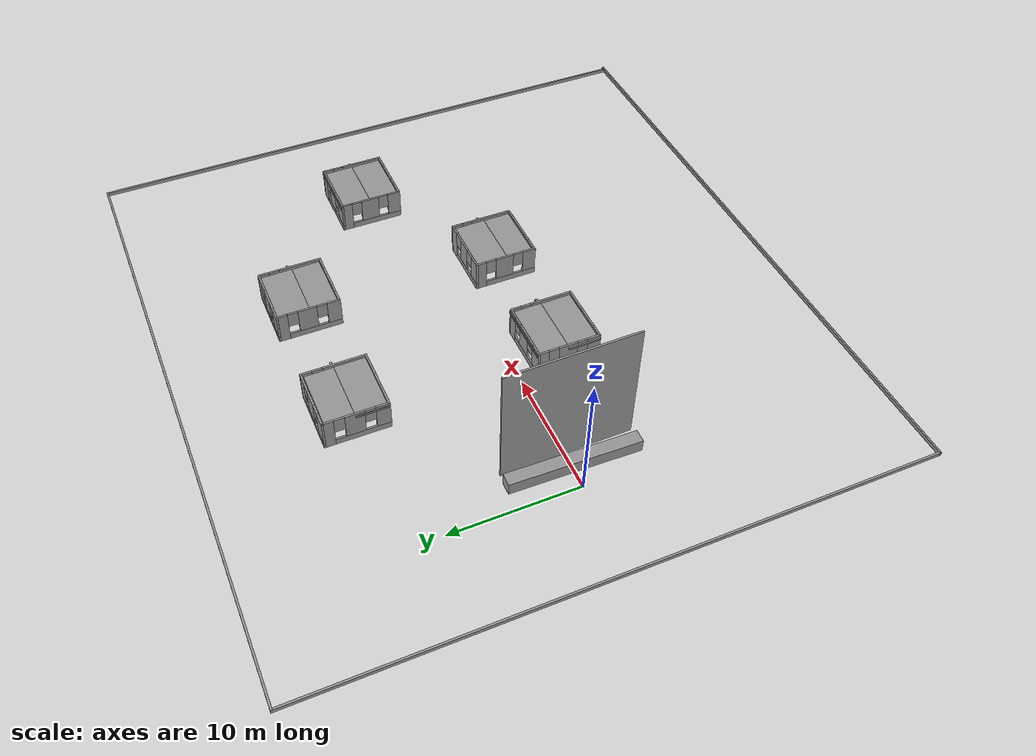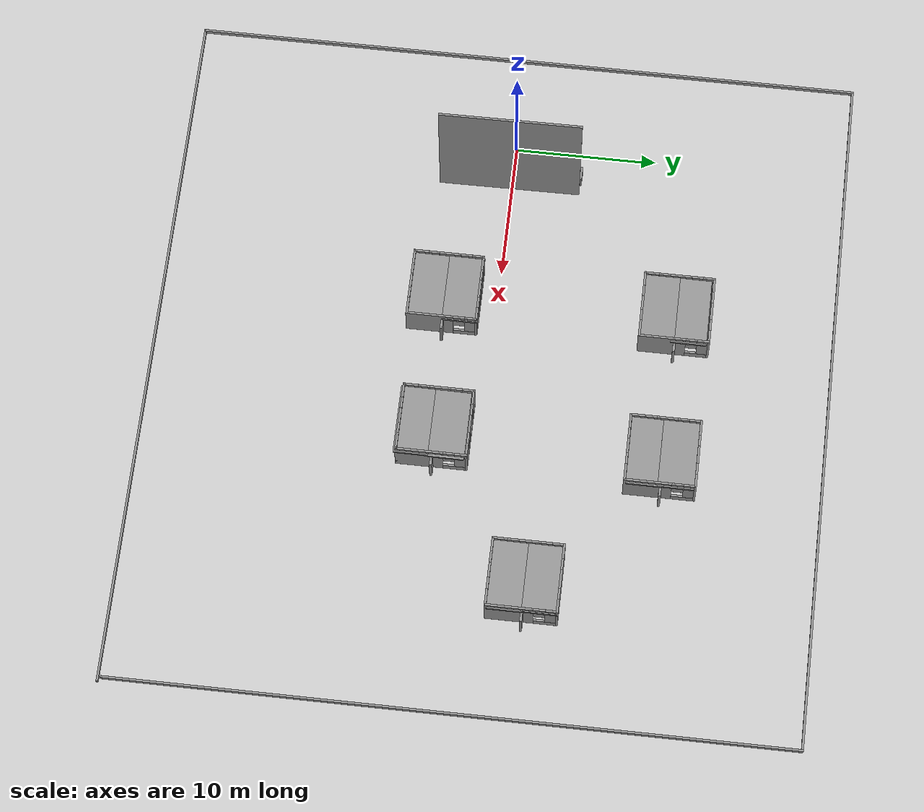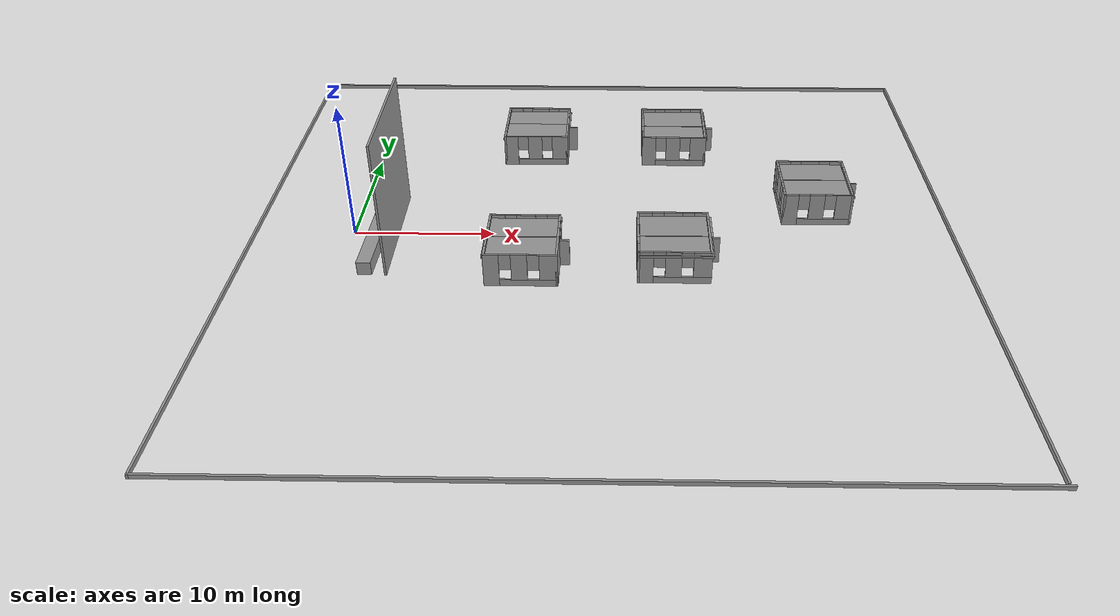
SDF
<sdf version="1.7">
 <world name="default">
  <physics name="default_physics" default="0" type="ode">
   <ode>
    <solver>
     <type>quick</type>
     <iters>100</iters>
     <sor>1</sor>
     <use_dynamic_moi_rescaling>0</use_dynamic_moi_rescaling>
    </solver>
    <constraints>
     <cfm>0</cfm>
     <erp>0.2</erp>
     <contact_max_correcting_vel>0.1</contact_max_correcting_vel>
     <contact_surface_layer>0</contact_surface_layer>
    </constraints>
   </ode>
   <real_time_update_rate>-1</real_time_update_rate>
   <max_step_size>0.001</max_step_size>
   <real_time_factor>1</real_time_factor>
  </physics>
  <gravity>0 0 -9.8</gravity>
  <light name="sun" type="directional">
   <pose>0 0 10 0 -0 0</pose>
   <diffuse>0.8 0.8 0.8 1</diffuse>
   <specular>0.2 0.2 0.2 1</specular>
   <attenuation>
    <range>1000</range>
    <constant>0.9</constant>
    <linear>0.01</linear>
    <quadratic>0.001</quadratic>
   </attenuation>
   <direction>-0.5 0.1 -0.9</direction>
   <spot><inner_angle>0</inner_angle><outer_angle>0</outer_angle><falloff>0</falloff></spot>
  </light>
  <model name="ground_plane">
   <static>1</static>
   <link name="link">
    <collision name="collision">
     <geometry><plane><normal>0 0 1</normal><size>5000 5000</size></plane></geometry>
     <surface><friction><ode><mu>100</mu><mu2>50</mu2></ode></friction></surface>
    </collision>
   </link>
  </model>
  <magnetic_field>6e-06 2.3e-05 -4.2e-05</magnetic_field>
  <atmosphere type="adiabatic"/>
  <scene><ambient>0.4 0.4 0.4 1</ambient><background>0.7 0.7 0.7 1</background><shadows>1</shadows></scene>
  <audio><device>default</device></audio>
  <spherical_coordinates>
   <surface_model>EARTH_WGS84</surface_model>
   <latitude_deg>0</latitude_deg>
   <longitude_deg>0</longitude_deg>
   <elevation>0</elevation>
   <heading_deg>0</heading_deg>
  </spherical_coordinates>
  <model name="wall50m">
   <pose>17.9974 0.0206 0 0 -0 0</pose>
   <link name="Wall_4">
    <collision name="Wall_4_Collision">
     <geometry><box><size>50.5 0.15 0.3</size></box></geometry>
     <pose>0 0 0.15 0 -0 0</pose>
    </collision>
    <visual name="Wall_4_Visual">
     <pose>0 0 0.15 0 -0 0</pose>
     <geometry><box><size>50.5 0.15 0.3</size></box></geometry>
     <material>
      <script><uri>file://media/materials/scripts/gazebo.material</uri><name>Gazebo/Grey</name></script>
      <ambient>1 1 1 1</ambient>
     </material>
     <meta><layer>0</layer></meta>
    </visual>
    <pose>2e-06 -23.675 0 0 -0 3.14159</pose>
   </link>
   <link name="Wall_5">
    <collision name="Wall_5_Collision">
     <geometry><box><size>47.5 0.15 0.3</size></box></geometry>
     <pose>0 0 0.15 0 -0 0</pose>
    </collision>
    <visual name="Wall_5_Visual">
     <pose>0 0 0.15 0 -0 0</pose>
     <geometry><box><size>47.5 0.15 0.3</size></box></geometry>
     <material>
      <script><uri>file://media/materials/scripts/gazebo.material</uri><name>Gazebo/Grey</name></script>
      <ambient>1 1 1 1</ambient>
     </material>
     <meta><layer>0</layer></meta>
    </visual>
    <pose>-25.175 -0 0 0 -0 1.5708</pose>
   </link>
   <link name="Wall_6">
    <collision name="Wall_6_Collision">
     <geometry><box><size>50.25 0.15 0.3</size></box></geometry>
     <pose>0 0 0.15 0 -0 0</pose>
    </collision>
    <visual name="Wall_6_Visual">
     <pose>0 0 0.15 0 -0 0</pose>
     <geometry><box><size>50.25 0.15 0.3</size></box></geometry>
     <material>
      <script><uri>file://media/materials/scripts/gazebo.material</uri><name>Gazebo/Grey</name></script>
      <ambient>1 1 1 1</ambient>
     </material>
     <meta><layer>0</layer></meta>
    </visual>
    <pose>-0.124998 23.675 0 0 -0 0</pose>
   </link>
   <link name="Wall_7">
    <collision name="Wall_7_Collision">
     <geometry><box><size>47.25 0.15 0.3</size></box></geometry>
     <pose>0 0 0.15 0 -0 0</pose>
    </collision>
    <visual name="Wall_7_Visual">
     <pose>0 0 0.15 0 -0 0</pose>
     <geometry><box><size>47.25 0.15 0.3</size></box></geometry>
     <material>
      <script><uri>file://media/materials/scripts/gazebo.material</uri><name>Gazebo/Grey</name></script>
      <ambient>1 1 1 1</ambient>
     </material>
     <meta><layer>0</layer></meta>
    </visual>
    <pose>24.925 0.125 0 0 -0 -1.5708</pose>
   </link>
   <static>1</static>
  </model>
  <model name="wall10m">
   <pose>3.10185 -0.181993 0 0 0 -1.56343</pose>
   <link name="Wall_0">
    <collision name="Wall_0_Collision">
     <geometry><box><size>10 0.15 10</size></box></geometry>
     <pose>0 0 5 0 -0 0</pose>
    </collision>
    <visual name="Wall_0_Visual">
     <pose>0 0 5 0 -0 0</pose>
     <geometry><box><size>10 0.15 10</size></box></geometry>
     <material>
      <script><uri>file://media/materials/scripts/gazebo.material</uri><name>Gazebo/Grey</name></script>
      <ambient>1 1 1 1</ambient>
     </material>
     <meta><layer>0</layer></meta>
    </visual>
   </link>
   <static>1</static>
  </model>
  <model name="Pacel_stand">
   <link name="link">
    <inertial>
     <mass>18.9585</mass>
     <inertia><ixx>3.15974</ixx><ixy>0</ixy><ixz>0</ixz><iyy>569.422</iyy><iyz>0</iyz><izz>569.422</izz></inertia>
    </inertial>
    <pose>4.44827 0.008738 0 0 -0 0</pose>
    <visual name="visual">
     <geometry><box><size>10 1 1</size></box></geometry>
     <material>
      <script><name>Gazebo/Grey</name><uri>file://media/materials/scripts/gazebo.material</uri></script>
      <shader type="vertex"><normal_map>__default__</normal_map></shader>
      <ambient>0.3 0.3 0.3 1</ambient>
      <diffuse>0.7 0.7 0.7 1</diffuse>
      <specular>0.01 0.01 0.01 1</specular>
      <emissive>0 0 0 1</emissive>
     </material>
    </visual>
    <collision name="collision">
     <geometry><box><size>9.99997 1 1</size></box></geometry>
     <surface>
      <friction>
       <ode><mu>1</mu><mu2>1</mu2><fdir1>0 0 0</fdir1><slip1>0</slip1><slip2>0</slip2></ode>
       <torsional>
        <coefficient>1</coefficient>
        <patch_radius>0</patch_radius>
        <surface_radius>0</surface_radius>
        <use_patch_radius>1</use_patch_radius>
        <ode><slip>0</slip></ode>
       </torsional>
      </friction>
      <bounce><restitution_coefficient>0</restitution_coefficient><threshold>1e+06</threshold></bounce>
      <contact>
       <collide_without_contact>0</collide_without_contact>
       <collide_without_contact_bitmask>1</collide_without_contact_bitmask>
       <collide_bitmask>1</collide_bitmask>
       <ode>
        <soft_cfm>0</soft_cfm>
        <soft_erp>0.2</soft_erp>
        <kp>1e+13</kp>
        <kd>1</kd>
        <max_vel>0.01</max_vel>
        <min_depth>0</min_depth>
       </ode>
       <bullet>
        <split_impulse>1</split_impulse>
        <split_impulse_penetration_threshold>-0.01</split_impulse_penetration_threshold>
        <soft_cfm>0</soft_cfm>
        <soft_erp>0.2</soft_erp>
        <kp>1e+13</kp>
        <kd>1</kd>
       </bullet>
      </contact>
     </surface>
    </collision>
   </link>
   <static>0</static>
   <pose>1.87633 4.35864 0.5 0 0 -1.592</pose>
  </model>
  <model name="5m">
   <pose>22.9189 -0.931863 2.17512 1.55349 -0 0</pose>
   <link name="Wall_0">
    <collision name="Wall_0_Collision">
     <geometry><box><size>5 0.15 2.5</size></box></geometry>
     <pose>0 0 1.25 0 -0 0</pose>
    </collision>
    <visual name="Wall_0_Visual">
     <pose>0 0 1.25 0 -0 0</pose>
     <geometry><box><size>5 0.15 2.5</size></box></geometry>
     <material>
      <script><uri>file://media/materials/scripts/gazebo.material</uri><name>Gazebo/Grey</name></script>
      <ambient>1 1 1 1</ambient>
     </material>
     <meta><layer>0</layer></meta>
    </visual>
   </link>
   <static>1</static>
  </model>
  <model name="House">
   <pose>12.4099 12.5509 0 0 -0 0</pose>
   <link name="Door_0">
    <collision name="Door_0_Collision">
     <geometry><box><size>0.9 0.17 2</size></box></geometry>
     <pose>0 0 1 0 -0 0</pose>
    </collision>
    <visual name="Door_0_Visual">
     <pose>0 0 1 0 -0 0</pose>
     <geometry><box><size>0.9 0.17 2</size></box></geometry>
     <material>
      <script><uri>file://media/materials/scripts/gazebo.material</uri><name>Gazebo/Grey</name></script>
     </material>
    </visual>
    <pose>2.72267 0.051323 0 0 -0 0</pose>
   </link>
   <link name="Wall_2">
    <pose>0 2.425 0 0 -0 3.14159</pose>
    <visual name="Wall_2_Visual_0">
     <pose>-2.01333 0 1.25 0 -0 0</pose>
     <geometry><box><size>0.973339 0.15 2.5</size></box></geometry>
     <material>
      <script><uri>file://media/materials/scripts/gazebo.material</uri><name>Gazebo/Grey</name></script>
      <ambient>1 1 1 1</ambient>
     </material>
     <meta><layer>0</layer></meta>
    </visual>
    <collision name="Wall_2_Collision_0">
     <geometry><box><size>0.973339 0.15 2.5</size></box></geometry>
     <pose>-2.01333 0 1.25 0 -0 0</pose>
    </collision>
    <visual name="Wall_2_Visual_1">
     <pose>0.48667 0 0.25 0 -0 0</pose>
     <geometry><box><size>4.02666 0.15 0.5</size></box></geometry>
     <material>
      <script><uri>file://media/materials/scripts/gazebo.material</uri><name>Gazebo/Grey</name></script>
      <ambient>1 1 1 1</ambient>
     </material>
     <meta><layer>0</layer></meta>
    </visual>
    <collision name="Wall_2_Collision_1">
     <geometry><box><size>4.02666 0.15 0.5</size></box></geometry>
     <pose>0.48667 0 0.25 0 -0 0</pose>
    </collision>
    <visual name="Wall_2_Visual_2">
     <pose>-0.062653 0 1.5 0 -0 0</pose>
     <geometry><box><size>1.32802 0.15 2</size></box></geometry>
     <material>
      <script><uri>file://media/materials/scripts/gazebo.material</uri><name>Gazebo/Grey</name></script>
      <ambient>1 1 1 1</ambient>
     </material>
     <meta><layer>0</layer></meta>
    </visual>
    <collision name="Wall_2_Collision_2">
     <geometry><box><size>1.32802 0.15 2</size></box></geometry>
     <pose>-0.062653 0 1.5 0 -0 0</pose>
    </collision>
    <visual name="Wall_2_Visual_3">
     <pose>1.95068 0 1.5 0 -0 0</pose>
     <geometry><box><size>1.09865 0.15 2</size></box></geometry>
     <material>
      <script><uri>file://media/materials/scripts/gazebo.material</uri><name>Gazebo/Grey</name></script>
      <ambient>1 1 1 1</ambient>
     </material>
     <meta><layer>0</layer></meta>
    </visual>
    <collision name="Wall_2_Collision_3">
     <geometry><box><size>1.09865 0.15 2</size></box></geometry>
     <pose>1.95068 0 1.5 0 -0 0</pose>
    </collision>
    <visual name="Wall_2_Visual_4">
     <pose>-1.12666 0 1.9 0 -0 0</pose>
     <geometry><box><size>0.8 0.15 1.2</size></box></geometry>
     <material>
      <script><uri>file://media/materials/scripts/gazebo.material</uri><name>Gazebo/Grey</name></script>
      <ambient>1 1 1 1</ambient>
     </material>
     <meta><layer>0</layer></meta>
    </visual>
    <collision name="Wall_2_Collision_4">
     <geometry><box><size>0.8 0.15 1.2</size></box></geometry>
     <pose>-1.12666 0 1.9 0 -0 0</pose>
    </collision>
    <visual name="Wall_2_Visual_5">
     <pose>1.00135 0 1.9 0 -0 0</pose>
     <geometry><box><size>0.8 0.15 1.2</size></box></geometry>
     <material>
      <script><uri>file://media/materials/scripts/gazebo.material</uri><name>Gazebo/Grey</name></script>
      <ambient>1 1 1 1</ambient>
     </material>
     <meta><layer>0</layer></meta>
    </visual>
    <collision name="Wall_2_Collision_5">
     <geometry><box><size>0.8 0.15 1.2</size></box></geometry>
     <pose>1.00135 0 1.9 0 -0 0</pose>
    </collision>
   </link>
   <link name="Wall_3">
    <pose>-2.425 0 0 0 -0 -1.5708</pose>
    <visual name="Wall_3_Visual_0">
     <pose>-2.06087 0 1.25 0 -0 0</pose>
     <geometry><box><size>0.878268 0.15 2.5</size></box></geometry>
     <material>
      <script><uri>file://media/materials/scripts/gazebo.material</uri><name>Gazebo/Grey</name></script>
      <ambient>1 1 1 1</ambient>
     </material>
     <meta><layer>0</layer></meta>
    </visual>
    <collision name="Wall_3_Collision_0">
     <geometry><box><size>0.878268 0.15 2.5</size></box></geometry>
     <pose>-2.06087 0 1.25 0 -0 0</pose>
    </collision>
    <visual name="Wall_3_Visual_1">
     <pose>0.439134 0 0.25 0 -0 0</pose>
     <geometry><box><size>4.12173 0.15 0.5</size></box></geometry>
     <material>
      <script><uri>file://media/materials/scripts/gazebo.material</uri><name>Gazebo/Grey</name></script>
      <ambient>1 1 1 1</ambient>
     </material>
     <meta><layer>0</layer></meta>
    </visual>
    <collision name="Wall_3_Collision_1">
     <geometry><box><size>4.12173 0.15 0.5</size></box></geometry>
     <pose>0.439134 0 0.25 0 -0 0</pose>
    </collision>
    <visual name="Wall_3_Visual_2">
     <pose>-0.091224 0 1.5 0 -0 0</pose>
     <geometry><box><size>1.46102 0.15 2</size></box></geometry>
     <material>
      <script><uri>file://media/materials/scripts/gazebo.material</uri><name>Gazebo/Grey</name></script>
      <ambient>1 1 1 1</ambient>
     </material>
     <meta><layer>0</layer></meta>
    </visual>
    <collision name="Wall_3_Collision_2">
     <geometry><box><size>1.46102 0.15 2</size></box></geometry>
     <pose>-0.091224 0 1.5 0 -0 0</pose>
    </collision>
    <visual name="Wall_3_Visual_3">
     <pose>1.96964 0 1.5 0 -0 0</pose>
     <geometry><box><size>1.06072 0.15 2</size></box></geometry>
     <material>
      <script><uri>file://media/materials/scripts/gazebo.material</uri><name>Gazebo/Grey</name></script>
      <ambient>1 1 1 1</ambient>
     </material>
     <meta><layer>0</layer></meta>
    </visual>
    <collision name="Wall_3_Collision_3">
     <geometry><box><size>1.06072 0.15 2</size></box></geometry>
     <pose>1.96964 0 1.5 0 -0 0</pose>
    </collision>
    <visual name="Wall_3_Visual_4">
     <pose>-1.22173 0 1.9 0 -0 0</pose>
     <geometry><box><size>0.8 0.15 1.2</size></box></geometry>
     <material>
      <script><uri>file://media/materials/scripts/gazebo.material</uri><name>Gazebo/Grey</name></script>
      <ambient>1 1 1 1</ambient>
     </material>
     <meta><layer>0</layer></meta>
    </visual>
    <collision name="Wall_3_Collision_4">
     <geometry><box><size>0.8 0.15 1.2</size></box></geometry>
     <pose>-1.22173 0 1.9 0 -0 0</pose>
    </collision>
    <visual name="Wall_3_Visual_5">
     <pose>1.03929 0 1.9 0 -0 0</pose>
     <geometry><box><size>0.8 0.15 1.2</size></box></geometry>
     <material>
      <script><uri>file://media/materials/scripts/gazebo.material</uri><name>Gazebo/Grey</name></script>
      <ambient>1 1 1 1</ambient>
     </material>
     <meta><layer>0</layer></meta>
    </visual>
    <collision name="Wall_3_Collision_5">
     <geometry><box><size>0.8 0.15 1.2</size></box></geometry>
     <pose>1.03929 0 1.9 0 -0 0</pose>
    </collision>
   </link>
   <link name="Wall_4">
    <pose>0 -2.425 0 0 -0 0</pose>
    <visual name="Wall_4_Visual_0">
     <pose>-1.96398 0 1.25 0 -0 0</pose>
     <geometry><box><size>1.07204 0.15 2.5</size></box></geometry>
     <material>
      <script><uri>file://media/materials/scripts/gazebo.material</uri><name>Gazebo/Grey</name></script>
      <ambient>1 1 1 1</ambient>
     </material>
     <meta><layer>0</layer></meta>
    </visual>
    <collision name="Wall_4_Collision_0">
     <geometry><box><size>1.07204 0.15 2.5</size></box></geometry>
     <pose>-1.96398 0 1.25 0 -0 0</pose>
    </collision>
    <visual name="Wall_4_Visual_1">
     <pose>0.536022 0 0.25 0 -0 0</pose>
     <geometry><box><size>3.92796 0.15 0.5</size></box></geometry>
     <material>
      <script><uri>file://media/materials/scripts/gazebo.material</uri><name>Gazebo/Grey</name></script>
      <ambient>1 1 1 1</ambient>
     </material>
     <meta><layer>0</layer></meta>
    </visual>
    <collision name="Wall_4_Collision_1">
     <geometry><box><size>3.92796 0.15 0.5</size></box></geometry>
     <pose>0.536022 0 0.25 0 -0 0</pose>
    </collision>
    <visual name="Wall_4_Visual_2">
     <pose>-0.083648 0 1.5 0 -0 0</pose>
     <geometry><box><size>1.08861 0.15 2</size></box></geometry>
     <material>
      <script><uri>file://media/materials/scripts/gazebo.material</uri><name>Gazebo/Grey</name></script>
      <ambient>1 1 1 1</ambient>
     </material>
     <meta><layer>0</layer></meta>
    </visual>
    <collision name="Wall_4_Collision_2">
     <geometry><box><size>1.08861 0.15 2</size></box></geometry>
     <pose>-0.083648 0 1.5 0 -0 0</pose>
    </collision>
    <visual name="Wall_4_Visual_3">
     <pose>1.88033 0 1.5 0 -0 0</pose>
     <geometry><box><size>1.23934 0.15 2</size></box></geometry>
     <material>
      <script><uri>file://media/materials/scripts/gazebo.material</uri><name>Gazebo/Grey</name></script>
      <ambient>1 1 1 1</ambient>
     </material>
     <meta><layer>0</layer></meta>
    </visual>
    <collision name="Wall_4_Collision_3">
     <geometry><box><size>1.23934 0.15 2</size></box></geometry>
     <pose>1.88033 0 1.5 0 -0 0</pose>
    </collision>
    <visual name="Wall_4_Visual_4">
     <pose>-1.02796 0 1.9 0 -0 0</pose>
     <geometry><box><size>0.8 0.15 1.2</size></box></geometry>
     <material>
      <script><uri>file://media/materials/scripts/gazebo.material</uri><name>Gazebo/Grey</name></script>
      <ambient>1 1 1 1</ambient>
     </material>
     <meta><layer>0</layer></meta>
    </visual>
    <collision name="Wall_4_Collision_4">
     <geometry><box><size>0.8 0.15 1.2</size></box></geometry>
     <pose>-1.02796 0 1.9 0 -0 0</pose>
    </collision>
    <visual name="Wall_4_Visual_5">
     <pose>0.860659 0 1.9 0 -0 0</pose>
     <geometry><box><size>0.8 0.15 1.2</size></box></geometry>
     <material>
      <script><uri>file://media/materials/scripts/gazebo.material</uri><name>Gazebo/Grey</name></script>
      <ambient>1 1 1 1</ambient>
     </material>
     <meta><layer>0</layer></meta>
    </visual>
    <collision name="Wall_4_Collision_5">
     <geometry><box><size>0.8 0.15 1.2</size></box></geometry>
     <pose>0.860659 0 1.9 0 -0 0</pose>
    </collision>
   </link>
   <link name="Wall_5">
    <pose>2.425 0 0 0 -0 1.5708</pose>
    <visual name="Wall_5_Visual_0">
     <pose>-0.839134 0 1.25 0 -0 0</pose>
     <geometry><box><size>3.32173 0.15 2.5</size></box></geometry>
     <material>
      <script><uri>file://media/materials/scripts/gazebo.material</uri><name>Gazebo/Grey</name></script>
      <ambient>1 1 1 1</ambient>
     </material>
     <meta><layer>0</layer></meta>
    </visual>
    <collision name="Wall_5_Collision_0">
     <geometry><box><size>3.32173 0.15 2.5</size></box></geometry>
     <pose>-0.839134 0 1.25 0 -0 0</pose>
    </collision>
    <visual name="Wall_5_Visual_1">
     <pose>1.66087 0 0.25 0 -0 0</pose>
     <geometry><box><size>1.67827 0.15 0.5</size></box></geometry>
     <material>
      <script><uri>file://media/materials/scripts/gazebo.material</uri><name>Gazebo/Grey</name></script>
      <ambient>1 1 1 1</ambient>
     </material>
     <meta><layer>0</layer></meta>
    </visual>
    <collision name="Wall_5_Collision_1">
     <geometry><box><size>1.67827 0.15 0.5</size></box></geometry>
     <pose>1.66087 0 0.25 0 -0 0</pose>
    </collision>
    <visual name="Wall_5_Visual_2">
     <pose>2.06087 0 1.5 0 -0 0</pose>
     <geometry><box><size>0.878268 0.15 2</size></box></geometry>
     <material>
      <script><uri>file://media/materials/scripts/gazebo.material</uri><name>Gazebo/Grey</name></script>
      <ambient>1 1 1 1</ambient>
     </material>
     <meta><layer>0</layer></meta>
    </visual>
    <collision name="Wall_5_Collision_2">
     <geometry><box><size>0.878268 0.15 2</size></box></geometry>
     <pose>2.06087 0 1.5 0 -0 0</pose>
    </collision>
    <visual name="Wall_5_Visual_3">
     <pose>1.22173 0 1.9 0 -0 0</pose>
     <geometry><box><size>0.8 0.15 1.2</size></box></geometry>
     <material>
      <script><uri>file://media/materials/scripts/gazebo.material</uri><name>Gazebo/Grey</name></script>
      <ambient>1 1 1 1</ambient>
     </material>
     <meta><layer>0</layer></meta>
    </visual>
    <collision name="Wall_5_Collision_3">
     <geometry><box><size>0.8 0.15 1.2</size></box></geometry>
     <pose>1.22173 0 1.9 0 -0 0</pose>
    </collision>
   </link>
   <static>1</static>
  </model>
  <model name="5m_clone">
   <pose>12.3572 10.0911 2.23803 -1.57239 0 0</pose>
   <link name="Wall_0">
    <collision name="Wall_0_Collision">
     <geometry><box><size>5 0.15 2.5</size></box></geometry>
     <pose>0 0 1.25 0 -0 0</pose>
    </collision>
    <visual name="Wall_0_Visual">
     <pose>0 0 1.25 0 -0 0</pose>
     <geometry><box><size>5 0.15 2.5</size></box></geometry>
     <material>
      <script><uri>file://media/materials/scripts/gazebo.material</uri><name>Gazebo/Grey</name></script>
      <ambient>1 1 1 1</ambient>
     </material>
     <meta><layer>0</layer></meta>
    </visual>
   </link>
   <static>1</static>
  </model>
  <model name="House_0">
   <pose>23.3033 12.5521 0 0 -0 0</pose>
   <link name="Door_0">
    <collision name="Door_0_Collision">
     <geometry><box><size>0.9 0.17 2</size></box></geometry>
     <pose>0 0 1 0 -0 0</pose>
    </collision>
    <visual name="Door_0_Visual">
     <pose>0 0 1 0 -0 0</pose>
     <geometry><box><size>0.9 0.17 2</size></box></geometry>
     <material>
      <script><uri>file://media/materials/scripts/gazebo.material</uri><name>Gazebo/Grey</name></script>
     </material>
    </visual>
    <pose>2.72267 0.051323 0 0 -0 0</pose>
   </link>
   <link name="Wall_2">
    <pose>0 2.425 0 0 -0 3.14159</pose>
    <visual name="Wall_2_Visual_0">
     <pose>-2.01333 0 1.25 0 -0 0</pose>
     <geometry><box><size>0.973339 0.15 2.5</size></box></geometry>
     <material>
      <script><uri>file://media/materials/scripts/gazebo.material</uri><name>Gazebo/Grey</name></script>
      <ambient>1 1 1 1</ambient>
     </material>
     <meta><layer>0</layer></meta>
    </visual>
    <collision name="Wall_2_Collision_0">
     <geometry><box><size>0.973339 0.15 2.5</size></box></geometry>
     <pose>-2.01333 0 1.25 0 -0 0</pose>
    </collision>
    <visual name="Wall_2_Visual_1">
     <pose>0.48667 0 0.25 0 -0 0</pose>
     <geometry><box><size>4.02666 0.15 0.5</size></box></geometry>
     <material>
      <script><uri>file://media/materials/scripts/gazebo.material</uri><name>Gazebo/Grey</name></script>
      <ambient>1 1 1 1</ambient>
     </material>
     <meta><layer>0</layer></meta>
    </visual>
    <collision name="Wall_2_Collision_1">
     <geometry><box><size>4.02666 0.15 0.5</size></box></geometry>
     <pose>0.48667 0 0.25 0 -0 0</pose>
    </collision>
    <visual name="Wall_2_Visual_2">
     <pose>-0.062653 0 1.5 0 -0 0</pose>
     <geometry><box><size>1.32802 0.15 2</size></box></geometry>
     <material>
      <script><uri>file://media/materials/scripts/gazebo.material</uri><name>Gazebo/Grey</name></script>
      <ambient>1 1 1 1</ambient>
     </material>
     <meta><layer>0</layer></meta>
    </visual>
    <collision name="Wall_2_Collision_2">
     <geometry><box><size>1.32802 0.15 2</size></box></geometry>
     <pose>-0.062653 0 1.5 0 -0 0</pose>
    </collision>
    <visual name="Wall_2_Visual_3">
     <pose>1.95068 0 1.5 0 -0 0</pose>
     <geometry><box><size>1.09865 0.15 2</size></box></geometry>
     <material>
      <script><uri>file://media/materials/scripts/gazebo.material</uri><name>Gazebo/Grey</name></script>
      <ambient>1 1 1 1</ambient>
     </material>
     <meta><layer>0</layer></meta>
    </visual>
    <collision name="Wall_2_Collision_3">
     <geometry><box><size>1.09865 0.15 2</size></box></geometry>
     <pose>1.95068 0 1.5 0 -0 0</pose>
    </collision>
    <visual name="Wall_2_Visual_4">
     <pose>-1.12666 0 1.9 0 -0 0</pose>
     <geometry><box><size>0.8 0.15 1.2</size></box></geometry>
     <material>
      <script><uri>file://media/materials/scripts/gazebo.material</uri><name>Gazebo/Grey</name></script>
      <ambient>1 1 1 1</ambient>
     </material>
     <meta><layer>0</layer></meta>
    </visual>
    <collision name="Wall_2_Collision_4">
     <geometry><box><size>0.8 0.15 1.2</size></box></geometry>
     <pose>-1.12666 0 1.9 0 -0 0</pose>
    </collision>
    <visual name="Wall_2_Visual_5">
     <pose>1.00135 0 1.9 0 -0 0</pose>
     <geometry><box><size>0.8 0.15 1.2</size></box></geometry>
     <material>
      <script><uri>file://media/materials/scripts/gazebo.material</uri><name>Gazebo/Grey</name></script>
      <ambient>1 1 1 1</ambient>
     </material>
     <meta><layer>0</layer></meta>
    </visual>
    <collision name="Wall_2_Collision_5">
     <geometry><box><size>0.8 0.15 1.2</size></box></geometry>
     <pose>1.00135 0 1.9 0 -0 0</pose>
    </collision>
   </link>
   <link name="Wall_3">
    <pose>-2.425 0 0 0 -0 -1.5708</pose>
    <visual name="Wall_3_Visual_0">
     <pose>-2.06087 0 1.25 0 -0 0</pose>
     <geometry><box><size>0.878268 0.15 2.5</size></box></geometry>
     <material>
      <script><uri>file://media/materials/scripts/gazebo.material</uri><name>Gazebo/Grey</name></script>
      <ambient>1 1 1 1</ambient>
     </material>
     <meta><layer>0</layer></meta>
    </visual>
    <collision name="Wall_3_Collision_0">
     <geometry><box><size>0.878268 0.15 2.5</size></box></geometry>
     <pose>-2.06087 0 1.25 0 -0 0</pose>
    </collision>
    <visual name="Wall_3_Visual_1">
     <pose>0.439134 0 0.25 0 -0 0</pose>
     <geometry><box><size>4.12173 0.15 0.5</size></box></geometry>
     <material>
      <script><uri>file://media/materials/scripts/gazebo.material</uri><name>Gazebo/Grey</name></script>
      <ambient>1 1 1 1</ambient>
     </material>
     <meta><layer>0</layer></meta>
    </visual>
    <collision name="Wall_3_Collision_1">
     <geometry><box><size>4.12173 0.15 0.5</size></box></geometry>
     <pose>0.439134 0 0.25 0 -0 0</pose>
    </collision>
    <visual name="Wall_3_Visual_2">
     <pose>-0.091224 0 1.5 0 -0 0</pose>
     <geometry><box><size>1.46102 0.15 2</size></box></geometry>
     <material>
      <script><uri>file://media/materials/scripts/gazebo.material</uri><name>Gazebo/Grey</name></script>
      <ambient>1 1 1 1</ambient>
     </material>
     <meta><layer>0</layer></meta>
    </visual>
    <collision name="Wall_3_Collision_2">
     <geometry><box><size>1.46102 0.15 2</size></box></geometry>
     <pose>-0.091224 0 1.5 0 -0 0</pose>
    </collision>
    <visual name="Wall_3_Visual_3">
     <pose>1.96964 0 1.5 0 -0 0</pose>
     <geometry><box><size>1.06072 0.15 2</size></box></geometry>
     <material>
      <script><uri>file://media/materials/scripts/gazebo.material</uri><name>Gazebo/Grey</name></script>
      <ambient>1 1 1 1</ambient>
     </material>
     <meta><layer>0</layer></meta>
    </visual>
    <collision name="Wall_3_Collision_3">
     <geometry><box><size>1.06072 0.15 2</size></box></geometry>
     <pose>1.96964 0 1.5 0 -0 0</pose>
    </collision>
    <visual name="Wall_3_Visual_4">
     <pose>-1.22173 0 1.9 0 -0 0</pose>
     <geometry><box><size>0.8 0.15 1.2</size></box></geometry>
     <material>
      <script><uri>file://media/materials/scripts/gazebo.material</uri><name>Gazebo/Grey</name></script>
      <ambient>1 1 1 1</ambient>
     </material>
     <meta><layer>0</layer></meta>
    </visual>
    <collision name="Wall_3_Collision_4">
     <geometry><box><size>0.8 0.15 1.2</size></box></geometry>
     <pose>-1.22173 0 1.9 0 -0 0</pose>
    </collision>
    <visual name="Wall_3_Visual_5">
     <pose>1.03929 0 1.9 0 -0 0</pose>
     <geometry><box><size>0.8 0.15 1.2</size></box></geometry>
     <material>
      <script><uri>file://media/materials/scripts/gazebo.material</uri><name>Gazebo/Grey</name></script>
      <ambient>1 1 1 1</ambient>
     </material>
     <meta><layer>0</layer></meta>
    </visual>
    <collision name="Wall_3_Collision_5">
     <geometry><box><size>0.8 0.15 1.2</size></box></geometry>
     <pose>1.03929 0 1.9 0 -0 0</pose>
    </collision>
   </link>
   <link name="Wall_4">
    <pose>0 -2.425 0 0 -0 0</pose>
    <visual name="Wall_4_Visual_0">
     <pose>-1.96398 0 1.25 0 -0 0</pose>
     <geometry><box><size>1.07204 0.15 2.5</size></box></geometry>
     <material>
      <script><uri>file://media/materials/scripts/gazebo.material</uri><name>Gazebo/Grey</name></script>
      <ambient>1 1 1 1</ambient>
     </material>
     <meta><layer>0</layer></meta>
    </visual>
    <collision name="Wall_4_Collision_0">
     <geometry><box><size>1.07204 0.15 2.5</size></box></geometry>
     <pose>-1.96398 0 1.25 0 -0 0</pose>
    </collision>
    <visual name="Wall_4_Visual_1">
     <pose>0.536022 0 0.25 0 -0 0</pose>
     <geometry><box><size>3.92796 0.15 0.5</size></box></geometry>
     <material>
      <script><uri>file://media/materials/scripts/gazebo.material</uri><name>Gazebo/Grey</name></script>
      <ambient>1 1 1 1</ambient>
     </material>
     <meta><layer>0</layer></meta>
    </visual>
    <collision name="Wall_4_Collision_1">
     <geometry><box><size>3.92796 0.15 0.5</size></box></geometry>
     <pose>0.536022 0 0.25 0 -0 0</pose>
    </collision>
    <visual name="Wall_4_Visual_2">
     <pose>-0.083648 0 1.5 0 -0 0</pose>
     <geometry><box><size>1.08861 0.15 2</size></box></geometry>
     <material>
      <script><uri>file://media/materials/scripts/gazebo.material</uri><name>Gazebo/Grey</name></script>
      <ambient>1 1 1 1</ambient>
     </material>
     <meta><layer>0</layer></meta>
    </visual>
    <collision name="Wall_4_Collision_2">
     <geometry><box><size>1.08861 0.15 2</size></box></geometry>
     <pose>-0.083648 0 1.5 0 -0 0</pose>
    </collision>
    <visual name="Wall_4_Visual_3">
     <pose>1.88033 0 1.5 0 -0 0</pose>
     <geometry><box><size>1.23934 0.15 2</size></box></geometry>
     <material>
      <script><uri>file://media/materials/scripts/gazebo.material</uri><name>Gazebo/Grey</name></script>
      <ambient>1 1 1 1</ambient>
     </material>
     <meta><layer>0</layer></meta>
    </visual>
    <collision name="Wall_4_Collision_3">
     <geometry><box><size>1.23934 0.15 2</size></box></geometry>
     <pose>1.88033 0 1.5 0 -0 0</pose>
    </collision>
    <visual name="Wall_4_Visual_4">
     <pose>-1.02796 0 1.9 0 -0 0</pose>
     <geometry><box><size>0.8 0.15 1.2</size></box></geometry>
     <material>
      <script><uri>file://media/materials/scripts/gazebo.material</uri><name>Gazebo/Grey</name></script>
      <ambient>1 1 1 1</ambient>
     </material>
     <meta><layer>0</layer></meta>
    </visual>
    <collision name="Wall_4_Collision_4">
     <geometry><box><size>0.8 0.15 1.2</size></box></geometry>
     <pose>-1.02796 0 1.9 0 -0 0</pose>
    </collision>
    <visual name="Wall_4_Visual_5">
     <pose>0.860659 0 1.9 0 -0 0</pose>
     <geometry><box><size>0.8 0.15 1.2</size></box></geometry>
     <material>
      <script><uri>file://media/materials/scripts/gazebo.material</uri><name>Gazebo/Grey</name></script>
      <ambient>1 1 1 1</ambient>
     </material>
     <meta><layer>0</layer></meta>
    </visual>
    <collision name="Wall_4_Collision_5">
     <geometry><box><size>0.8 0.15 1.2</size></box></geometry>
     <pose>0.860659 0 1.9 0 -0 0</pose>
    </collision>
   </link>
   <link name="Wall_5">
    <pose>2.425 0 0 0 -0 1.5708</pose>
    <visual name="Wall_5_Visual_0">
     <pose>-0.839134 0 1.25 0 -0 0</pose>
     <geometry><box><size>3.32173 0.15 2.5</size></box></geometry>
     <material>
      <script><uri>file://media/materials/scripts/gazebo.material</uri><name>Gazebo/Grey</name></script>
      <ambient>1 1 1 1</ambient>
     </material>
     <meta><layer>0</layer></meta>
    </visual>
    <collision name="Wall_5_Collision_0">
     <geometry><box><size>3.32173 0.15 2.5</size></box></geometry>
     <pose>-0.839134 0 1.25 0 -0 0</pose>
    </collision>
    <visual name="Wall_5_Visual_1">
     <pose>1.66087 0 0.25 0 -0 0</pose>
     <geometry><box><size>1.67827 0.15 0.5</size></box></geometry>
     <material>
      <script><uri>file://media/materials/scripts/gazebo.material</uri><name>Gazebo/Grey</name></script>
      <ambient>1 1 1 1</ambient>
     </material>
     <meta><layer>0</layer></meta>
    </visual>
    <collision name="Wall_5_Collision_1">
     <geometry><box><size>1.67827 0.15 0.5</size></box></geometry>
     <pose>1.66087 0 0.25 0 -0 0</pose>
    </collision>
    <visual name="Wall_5_Visual_2">
     <pose>2.06087 0 1.5 0 -0 0</pose>
     <geometry><box><size>0.878268 0.15 2</size></box></geometry>
     <material>
      <script><uri>file://media/materials/scripts/gazebo.material</uri><name>Gazebo/Grey</name></script>
      <ambient>1 1 1 1</ambient>
     </material>
     <meta><layer>0</layer></meta>
    </visual>
    <collision name="Wall_5_Collision_2">
     <geometry><box><size>0.878268 0.15 2</size></box></geometry>
     <pose>2.06087 0 1.5 0 -0 0</pose>
    </collision>
    <visual name="Wall_5_Visual_3">
     <pose>1.22173 0 1.9 0 -0 0</pose>
     <geometry><box><size>0.8 0.15 1.2</size></box></geometry>
     <material>
      <script><uri>file://media/materials/scripts/gazebo.material</uri><name>Gazebo/Grey</name></script>
      <ambient>1 1 1 1</ambient>
     </material>
     <meta><layer>0</layer></meta>
    </visual>
    <collision name="Wall_5_Collision_3">
     <geometry><box><size>0.8 0.15 1.2</size></box></geometry>
     <pose>1.22173 0 1.9 0 -0 0</pose>
    </collision>
   </link>
   <static>1</static>
  </model>
  <model name="House_1">
   <pose>12.4567 -3.69962 0 0 -0 0</pose>
   <link name="Door_0">
    <collision name="Door_0_Collision">
     <geometry><box><size>0.9 0.17 2</size></box></geometry>
     <pose>0 0 1 0 -0 0</pose>
    </collision>
    <visual name="Door_0_Visual">
     <pose>0 0 1 0 -0 0</pose>
     <geometry><box><size>0.9 0.17 2</size></box></geometry>
     <material>
      <script><uri>file://media/materials/scripts/gazebo.material</uri><name>Gazebo/Grey</name></script>
     </material>
    </visual>
    <pose>2.72267 0.051323 0 0 -0 0</pose>
   </link>
   <link name="Wall_2">
    <pose>0 2.425 0 0 -0 3.14159</pose>
    <visual name="Wall_2_Visual_0">
     <pose>-2.01333 0 1.25 0 -0 0</pose>
     <geometry><box><size>0.973339 0.15 2.5</size></box></geometry>
     <material>
      <script><uri>file://media/materials/scripts/gazebo.material</uri><name>Gazebo/Grey</name></script>
      <ambient>1 1 1 1</ambient>
     </material>
     <meta><layer>0</layer></meta>
    </visual>
    <collision name="Wall_2_Collision_0">
     <geometry><box><size>0.973339 0.15 2.5</size></box></geometry>
     <pose>-2.01333 0 1.25 0 -0 0</pose>
    </collision>
    <visual name="Wall_2_Visual_1">
     <pose>0.48667 0 0.25 0 -0 0</pose>
     <geometry><box><size>4.02666 0.15 0.5</size></box></geometry>
     <material>
      <script><uri>file://media/materials/scripts/gazebo.material</uri><name>Gazebo/Grey</name></script>
      <ambient>1 1 1 1</ambient>
     </material>
     <meta><layer>0</layer></meta>
    </visual>
    <collision name="Wall_2_Collision_1">
     <geometry><box><size>4.02666 0.15 0.5</size></box></geometry>
     <pose>0.48667 0 0.25 0 -0 0</pose>
    </collision>
    <visual name="Wall_2_Visual_2">
     <pose>-0.062653 0 1.5 0 -0 0</pose>
     <geometry><box><size>1.32802 0.15 2</size></box></geometry>
     <material>
      <script><uri>file://media/materials/scripts/gazebo.material</uri><name>Gazebo/Grey</name></script>
      <ambient>1 1 1 1</ambient>
     </material>
     <meta><layer>0</layer></meta>
    </visual>
    <collision name="Wall_2_Collision_2">
     <geometry><box><size>1.32802 0.15 2</size></box></geometry>
     <pose>-0.062653 0 1.5 0 -0 0</pose>
    </collision>
    <visual name="Wall_2_Visual_3">
     <pose>1.95068 0 1.5 0 -0 0</pose>
     <geometry><box><size>1.09865 0.15 2</size></box></geometry>
     <material>
      <script><uri>file://media/materials/scripts/gazebo.material</uri><name>Gazebo/Grey</name></script>
      <ambient>1 1 1 1</ambient>
     </material>
     <meta><layer>0</layer></meta>
    </visual>
    <collision name="Wall_2_Collision_3">
     <geometry><box><size>1.09865 0.15 2</size></box></geometry>
     <pose>1.95068 0 1.5 0 -0 0</pose>
    </collision>
    <visual name="Wall_2_Visual_4">
     <pose>-1.12666 0 1.9 0 -0 0</pose>
     <geometry><box><size>0.8 0.15 1.2</size></box></geometry>
     <material>
      <script><uri>file://media/materials/scripts/gazebo.material</uri><name>Gazebo/Grey</name></script>
      <ambient>1 1 1 1</ambient>
     </material>
     <meta><layer>0</layer></meta>
    </visual>
    <collision name="Wall_2_Collision_4">
     <geometry><box><size>0.8 0.15 1.2</size></box></geometry>
     <pose>-1.12666 0 1.9 0 -0 0</pose>
    </collision>
    <visual name="Wall_2_Visual_5">
     <pose>1.00135 0 1.9 0 -0 0</pose>
     <geometry><box><size>0.8 0.15 1.2</size></box></geometry>
     <material>
      <script><uri>file://media/materials/scripts/gazebo.material</uri><name>Gazebo/Grey</name></script>
      <ambient>1 1 1 1</ambient>
     </material>
     <meta><layer>0</layer></meta>
    </visual>
    <collision name="Wall_2_Collision_5">
     <geometry><box><size>0.8 0.15 1.2</size></box></geometry>
     <pose>1.00135 0 1.9 0 -0 0</pose>
    </collision>
   </link>
   <link name="Wall_3">
    <pose>-2.425 0 0 0 -0 -1.5708</pose>
    <visual name="Wall_3_Visual_0">
     <pose>-2.06087 0 1.25 0 -0 0</pose>
     <geometry><box><size>0.878268 0.15 2.5</size></box></geometry>
     <material>
      <script><uri>file://media/materials/scripts/gazebo.material</uri><name>Gazebo/Grey</name></script>
      <ambient>1 1 1 1</ambient>
     </material>
     <meta><layer>0</layer></meta>
    </visual>
    <collision name="Wall_3_Collision_0">
     <geometry><box><size>0.878268 0.15 2.5</size></box></geometry>
     <pose>-2.06087 0 1.25 0 -0 0</pose>
    </collision>
    <visual name="Wall_3_Visual_1">
     <pose>0.439134 0 0.25 0 -0 0</pose>
     <geometry><box><size>4.12173 0.15 0.5</size></box></geometry>
     <material>
      <script><uri>file://media/materials/scripts/gazebo.material</uri><name>Gazebo/Grey</name></script>
      <ambient>1 1 1 1</ambient>
     </material>
     <meta><layer>0</layer></meta>
    </visual>
    <collision name="Wall_3_Collision_1">
     <geometry><box><size>4.12173 0.15 0.5</size></box></geometry>
     <pose>0.439134 0 0.25 0 -0 0</pose>
    </collision>
    <visual name="Wall_3_Visual_2">
     <pose>-0.091224 0 1.5 0 -0 0</pose>
     <geometry><box><size>1.46102 0.15 2</size></box></geometry>
     <material>
      <script><uri>file://media/materials/scripts/gazebo.material</uri><name>Gazebo/Grey</name></script>
      <ambient>1 1 1 1</ambient>
     </material>
     <meta><layer>0</layer></meta>
    </visual>
    <collision name="Wall_3_Collision_2">
     <geometry><box><size>1.46102 0.15 2</size></box></geometry>
     <pose>-0.091224 0 1.5 0 -0 0</pose>
    </collision>
    <visual name="Wall_3_Visual_3">
     <pose>1.96964 0 1.5 0 -0 0</pose>
     <geometry><box><size>1.06072 0.15 2</size></box></geometry>
     <material>
      <script><uri>file://media/materials/scripts/gazebo.material</uri><name>Gazebo/Grey</name></script>
      <ambient>1 1 1 1</ambient>
     </material>
     <meta><layer>0</layer></meta>
    </visual>
    <collision name="Wall_3_Collision_3">
     <geometry><box><size>1.06072 0.15 2</size></box></geometry>
     <pose>1.96964 0 1.5 0 -0 0</pose>
    </collision>
    <visual name="Wall_3_Visual_4">
     <pose>-1.22173 0 1.9 0 -0 0</pose>
     <geometry><box><size>0.8 0.15 1.2</size></box></geometry>
     <material>
      <script><uri>file://media/materials/scripts/gazebo.material</uri><name>Gazebo/Grey</name></script>
      <ambient>1 1 1 1</ambient>
     </material>
     <meta><layer>0</layer></meta>
    </visual>
    <collision name="Wall_3_Collision_4">
     <geometry><box><size>0.8 0.15 1.2</size></box></geometry>
     <pose>-1.22173 0 1.9 0 -0 0</pose>
    </collision>
    <visual name="Wall_3_Visual_5">
     <pose>1.03929 0 1.9 0 -0 0</pose>
     <geometry><box><size>0.8 0.15 1.2</size></box></geometry>
     <material>
      <script><uri>file://media/materials/scripts/gazebo.material</uri><name>Gazebo/Grey</name></script>
      <ambient>1 1 1 1</ambient>
     </material>
     <meta><layer>0</layer></meta>
    </visual>
    <collision name="Wall_3_Collision_5">
     <geometry><box><size>0.8 0.15 1.2</size></box></geometry>
     <pose>1.03929 0 1.9 0 -0 0</pose>
    </collision>
   </link>
   <link name="Wall_4">
    <pose>0 -2.425 0 0 -0 0</pose>
    <visual name="Wall_4_Visual_0">
     <pose>-1.96398 0 1.25 0 -0 0</pose>
     <geometry><box><size>1.07204 0.15 2.5</size></box></geometry>
     <material>
      <script><uri>file://media/materials/scripts/gazebo.material</uri><name>Gazebo/Grey</name></script>
      <ambient>1 1 1 1</ambient>
     </material>
     <meta><layer>0</layer></meta>
    </visual>
    <collision name="Wall_4_Collision_0">
     <geometry><box><size>1.07204 0.15 2.5</size></box></geometry>
     <pose>-1.96398 0 1.25 0 -0 0</pose>
    </collision>
    <visual name="Wall_4_Visual_1">
     <pose>0.536022 0 0.25 0 -0 0</pose>
     <geometry><box><size>3.92796 0.15 0.5</size></box></geometry>
     <material>
      <script><uri>file://media/materials/scripts/gazebo.material</uri><name>Gazebo/Grey</name></script>
      <ambient>1 1 1 1</ambient>
     </material>
     <meta><layer>0</layer></meta>
    </visual>
    <collision name="Wall_4_Collision_1">
     <geometry><box><size>3.92796 0.15 0.5</size></box></geometry>
     <pose>0.536022 0 0.25 0 -0 0</pose>
    </collision>
    <visual name="Wall_4_Visual_2">
     <pose>-0.083648 0 1.5 0 -0 0</pose>
     <geometry><box><size>1.08861 0.15 2</size></box></geometry>
     <material>
      <script><uri>file://media/materials/scripts/gazebo.material</uri><name>Gazebo/Grey</name></script>
      <ambient>1 1 1 1</ambient>
     </material>
     <meta><layer>0</layer></meta>
    </visual>
    <collision name="Wall_4_Collision_2">
     <geometry><box><size>1.08861 0.15 2</size></box></geometry>
     <pose>-0.083648 0 1.5 0 -0 0</pose>
    </collision>
    <visual name="Wall_4_Visual_3">
     <pose>1.88033 0 1.5 0 -0 0</pose>
     <geometry><box><size>1.23934 0.15 2</size></box></geometry>
     <material>
      <script><uri>file://media/materials/scripts/gazebo.material</uri><name>Gazebo/Grey</name></script>
      <ambient>1 1 1 1</ambient>
     </material>
     <meta><layer>0</layer></meta>
    </visual>
    <collision name="Wall_4_Collision_3">
     <geometry><box><size>1.23934 0.15 2</size></box></geometry>
     <pose>1.88033 0 1.5 0 -0 0</pose>
    </collision>
    <visual name="Wall_4_Visual_4">
     <pose>-1.02796 0 1.9 0 -0 0</pose>
     <geometry><box><size>0.8 0.15 1.2</size></box></geometry>
     <material>
      <script><uri>file://media/materials/scripts/gazebo.material</uri><name>Gazebo/Grey</name></script>
      <ambient>1 1 1 1</ambient>
     </material>
     <meta><layer>0</layer></meta>
    </visual>
    <collision name="Wall_4_Collision_4">
     <geometry><box><size>0.8 0.15 1.2</size></box></geometry>
     <pose>-1.02796 0 1.9 0 -0 0</pose>
    </collision>
    <visual name="Wall_4_Visual_5">
     <pose>0.860659 0 1.9 0 -0 0</pose>
     <geometry><box><size>0.8 0.15 1.2</size></box></geometry>
     <material>
      <script><uri>file://media/materials/scripts/gazebo.material</uri><name>Gazebo/Grey</name></script>
      <ambient>1 1 1 1</ambient>
     </material>
     <meta><layer>0</layer></meta>
    </visual>
    <collision name="Wall_4_Collision_5">
     <geometry><box><size>0.8 0.15 1.2</size></box></geometry>
     <pose>0.860659 0 1.9 0 -0 0</pose>
    </collision>
   </link>
   <link name="Wall_5">
    <pose>2.425 0 0 0 -0 1.5708</pose>
    <visual name="Wall_5_Visual_0">
     <pose>-0.839134 0 1.25 0 -0 0</pose>
     <geometry><box><size>3.32173 0.15 2.5</size></box></geometry>
     <material>
      <script><uri>file://media/materials/scripts/gazebo.material</uri><name>Gazebo/Grey</name></script>
      <ambient>1 1 1 1</ambient>
     </material>
     <meta><layer>0</layer></meta>
    </visual>
    <collision name="Wall_5_Collision_0">
     <geometry><box><size>3.32173 0.15 2.5</size></box></geometry>
     <pose>-0.839134 0 1.25 0 -0 0</pose>
    </collision>
    <visual name="Wall_5_Visual_1">
     <pose>1.66087 0 0.25 0 -0 0</pose>
     <geometry><box><size>1.67827 0.15 0.5</size></box></geometry>
     <material>
      <script><uri>file://media/materials/scripts/gazebo.material</uri><name>Gazebo/Grey</name></script>
      <ambient>1 1 1 1</ambient>
     </material>
     <meta><layer>0</layer></meta>
    </visual>
    <collision name="Wall_5_Collision_1">
     <geometry><box><size>1.67827 0.15 0.5</size></box></geometry>
     <pose>1.66087 0 0.25 0 -0 0</pose>
    </collision>
    <visual name="Wall_5_Visual_2">
     <pose>2.06087 0 1.5 0 -0 0</pose>
     <geometry><box><size>0.878268 0.15 2</size></box></geometry>
     <material>
      <script><uri>file://media/materials/scripts/gazebo.material</uri><name>Gazebo/Grey</name></script>
      <ambient>1 1 1 1</ambient>
     </material>
     <meta><layer>0</layer></meta>
    </visual>
    <collision name="Wall_5_Collision_2">
     <geometry><box><size>0.878268 0.15 2</size></box></geometry>
     <pose>2.06087 0 1.5 0 -0 0</pose>
    </collision>
    <visual name="Wall_5_Visual_3">
     <pose>1.22173 0 1.9 0 -0 0</pose>
     <geometry><box><size>0.8 0.15 1.2</size></box></geometry>
     <material>
      <script><uri>file://media/materials/scripts/gazebo.material</uri><name>Gazebo/Grey</name></script>
      <ambient>1 1 1 1</ambient>
     </material>
     <meta><layer>0</layer></meta>
    </visual>
    <collision name="Wall_5_Collision_3">
     <geometry><box><size>0.8 0.15 1.2</size></box></geometry>
     <pose>1.22173 0 1.9 0 -0 0</pose>
    </collision>
   </link>
   <static>1</static>
  </model>
  <model name="House_2">
   <pose>22.7443 -3.22625 0 0 -0 0</pose>
   <link name="Door_0">
    <collision name="Door_0_Collision">
     <geometry><box><size>0.9 0.17 2</size></box></geometry>
     <pose>0 0 1 0 -0 0</pose>
    </collision>
    <visual name="Door_0_Visual">
     <pose>0 0 1 0 -0 0</pose>
     <geometry><box><size>0.9 0.17 2</size></box></geometry>
     <material>
      <script><uri>file://media/materials/scripts/gazebo.material</uri><name>Gazebo/Grey</name></script>
     </material>
    </visual>
    <pose>2.72267 0.051323 0 0 -0 0</pose>
   </link>
   <link name="Wall_2">
    <pose>0 2.425 0 0 -0 3.14159</pose>
    <visual name="Wall_2_Visual_0">
     <pose>-2.01333 0 1.25 0 -0 0</pose>
     <geometry><box><size>0.973339 0.15 2.5</size></box></geometry>
     <material>
      <script><uri>file://media/materials/scripts/gazebo.material</uri><name>Gazebo/Grey</name></script>
      <ambient>1 1 1 1</ambient>
     </material>
     <meta><layer>0</layer></meta>
    </visual>
    <collision name="Wall_2_Collision_0">
     <geometry><box><size>0.973339 0.15 2.5</size></box></geometry>
     <pose>-2.01333 0 1.25 0 -0 0</pose>
    </collision>
    <visual name="Wall_2_Visual_1">
     <pose>0.48667 0 0.25 0 -0 0</pose>
     <geometry><box><size>4.02666 0.15 0.5</size></box></geometry>
     <material>
      <script><uri>file://media/materials/scripts/gazebo.material</uri><name>Gazebo/Grey</name></script>
      <ambient>1 1 1 1</ambient>
     </material>
     <meta><layer>0</layer></meta>
    </visual>
    <collision name="Wall_2_Collision_1">
     <geometry><box><size>4.02666 0.15 0.5</size></box></geometry>
     <pose>0.48667 0 0.25 0 -0 0</pose>
    </collision>
    <visual name="Wall_2_Visual_2">
     <pose>-0.062653 0 1.5 0 -0 0</pose>
     <geometry><box><size>1.32802 0.15 2</size></box></geometry>
     <material>
      <script><uri>file://media/materials/scripts/gazebo.material</uri><name>Gazebo/Grey</name></script>
      <ambient>1 1 1 1</ambient>
     </material>
     <meta><layer>0</layer></meta>
    </visual>
    <collision name="Wall_2_Collision_2">
     <geometry><box><size>1.32802 0.15 2</size></box></geometry>
     <pose>-0.062653 0 1.5 0 -0 0</pose>
    </collision>
    <visual name="Wall_2_Visual_3">
     <pose>1.95068 0 1.5 0 -0 0</pose>
     <geometry><box><size>1.09865 0.15 2</size></box></geometry>
     <material>
      <script><uri>file://media/materials/scripts/gazebo.material</uri><name>Gazebo/Grey</name></script>
      <ambient>1 1 1 1</ambient>
     </material>
     <meta><layer>0</layer></meta>
    </visual>
    <collision name="Wall_2_Collision_3">
     <geometry><box><size>1.09865 0.15 2</size></box></geometry>
     <pose>1.95068 0 1.5 0 -0 0</pose>
    </collision>
    <visual name="Wall_2_Visual_4">
     <pose>-1.12666 0 1.9 0 -0 0</pose>
     <geometry><box><size>0.8 0.15 1.2</size></box></geometry>
     <material>
      <script><uri>file://media/materials/scripts/gazebo.material</uri><name>Gazebo/Grey</name></script>
      <ambient>1 1 1 1</ambient>
     </material>
     <meta><layer>0</layer></meta>
    </visual>
    <collision name="Wall_2_Collision_4">
     <geometry><box><size>0.8 0.15 1.2</size></box></geometry>
     <pose>-1.12666 0 1.9 0 -0 0</pose>
    </collision>
    <visual name="Wall_2_Visual_5">
     <pose>1.00135 0 1.9 0 -0 0</pose>
     <geometry><box><size>0.8 0.15 1.2</size></box></geometry>
     <material>
      <script><uri>file://media/materials/scripts/gazebo.material</uri><name>Gazebo/Grey</name></script>
      <ambient>1 1 1 1</ambient>
     </material>
     <meta><layer>0</layer></meta>
    </visual>
    <collision name="Wall_2_Collision_5">
     <geometry><box><size>0.8 0.15 1.2</size></box></geometry>
     <pose>1.00135 0 1.9 0 -0 0</pose>
    </collision>
   </link>
   <link name="Wall_3">
    <pose>-2.425 0 0 0 -0 -1.5708</pose>
    <visual name="Wall_3_Visual_0">
     <pose>-2.06087 0 1.25 0 -0 0</pose>
     <geometry><box><size>0.878268 0.15 2.5</size></box></geometry>
     <material>
      <script><uri>file://media/materials/scripts/gazebo.material</uri><name>Gazebo/Grey</name></script>
      <ambient>1 1 1 1</ambient>
     </material>
     <meta><layer>0</layer></meta>
    </visual>
    <collision name="Wall_3_Collision_0">
     <geometry><box><size>0.878268 0.15 2.5</size></box></geometry>
     <pose>-2.06087 0 1.25 0 -0 0</pose>
    </collision>
    <visual name="Wall_3_Visual_1">
     <pose>0.439134 0 0.25 0 -0 0</pose>
     <geometry><box><size>4.12173 0.15 0.5</size></box></geometry>
     <material>
      <script><uri>file://media/materials/scripts/gazebo.material</uri><name>Gazebo/Grey</name></script>
      <ambient>1 1 1 1</ambient>
     </material>
     <meta><layer>0</layer></meta>
    </visual>
    <collision name="Wall_3_Collision_1">
     <geometry><box><size>4.12173 0.15 0.5</size></box></geometry>
     <pose>0.439134 0 0.25 0 -0 0</pose>
    </collision>
    <visual name="Wall_3_Visual_2">
     <pose>-0.091224 0 1.5 0 -0 0</pose>
     <geometry><box><size>1.46102 0.15 2</size></box></geometry>
     <material>
      <script><uri>file://media/materials/scripts/gazebo.material</uri><name>Gazebo/Grey</name></script>
      <ambient>1 1 1 1</ambient>
     </material>
     <meta><layer>0</layer></meta>
    </visual>
    <collision name="Wall_3_Collision_2">
     <geometry><box><size>1.46102 0.15 2</size></box></geometry>
     <pose>-0.091224 0 1.5 0 -0 0</pose>
    </collision>
    <visual name="Wall_3_Visual_3">
     <pose>1.96964 0 1.5 0 -0 0</pose>
     <geometry><box><size>1.06072 0.15 2</size></box></geometry>
     <material>
      <script><uri>file://media/materials/scripts/gazebo.material</uri><name>Gazebo/Grey</name></script>
      <ambient>1 1 1 1</ambient>
     </material>
     <meta><layer>0</layer></meta>
    </visual>
    <collision name="Wall_3_Collision_3">
     <geometry><box><size>1.06072 0.15 2</size></box></geometry>
     <pose>1.96964 0 1.5 0 -0 0</pose>
    </collision>
    <visual name="Wall_3_Visual_4">
     <pose>-1.22173 0 1.9 0 -0 0</pose>
     <geometry><box><size>0.8 0.15 1.2</size></box></geometry>
     <material>
      <script><uri>file://media/materials/scripts/gazebo.material</uri><name>Gazebo/Grey</name></script>
      <ambient>1 1 1 1</ambient>
     </material>
     <meta><layer>0</layer></meta>
    </visual>
    <collision name="Wall_3_Collision_4">
     <geometry><box><size>0.8 0.15 1.2</size></box></geometry>
     <pose>-1.22173 0 1.9 0 -0 0</pose>
    </collision>
    <visual name="Wall_3_Visual_5">
     <pose>1.03929 0 1.9 0 -0 0</pose>
     <geometry><box><size>0.8 0.15 1.2</size></box></geometry>
     <material>
      <script><uri>file://media/materials/scripts/gazebo.material</uri><name>Gazebo/Grey</name></script>
      <ambient>1 1 1 1</ambient>
     </material>
     <meta><layer>0</layer></meta>
    </visual>
    <collision name="Wall_3_Collision_5">
     <geometry><box><size>0.8 0.15 1.2</size></box></geometry>
     <pose>1.03929 0 1.9 0 -0 0</pose>
    </collision>
   </link>
   <link name="Wall_4">
    <pose>0 -2.425 0 0 -0 0</pose>
    <visual name="Wall_4_Visual_0">
     <pose>-1.96398 0 1.25 0 -0 0</pose>
     <geometry><box><size>1.07204 0.15 2.5</size></box></geometry>
     <material>
      <script><uri>file://media/materials/scripts/gazebo.material</uri><name>Gazebo/Grey</name></script>
      <ambient>1 1 1 1</ambient>
     </material>
     <meta><layer>0</layer></meta>
    </visual>
    <collision name="Wall_4_Collision_0">
     <geometry><box><size>1.07204 0.15 2.5</size></box></geometry>
     <pose>-1.96398 0 1.25 0 -0 0</pose>
    </collision>
    <visual name="Wall_4_Visual_1">
     <pose>0.536022 0 0.25 0 -0 0</pose>
     <geometry><box><size>3.92796 0.15 0.5</size></box></geometry>
     <material>
      <script><uri>file://media/materials/scripts/gazebo.material</uri><name>Gazebo/Grey</name></script>
      <ambient>1 1 1 1</ambient>
     </material>
     <meta><layer>0</layer></meta>
    </visual>
    <collision name="Wall_4_Collision_1">
     <geometry><box><size>3.92796 0.15 0.5</size></box></geometry>
     <pose>0.536022 0 0.25 0 -0 0</pose>
    </collision>
    <visual name="Wall_4_Visual_2">
     <pose>-0.083648 0 1.5 0 -0 0</pose>
     <geometry><box><size>1.08861 0.15 2</size></box></geometry>
     <material>
      <script><uri>file://media/materials/scripts/gazebo.material</uri><name>Gazebo/Grey</name></script>
      <ambient>1 1 1 1</ambient>
     </material>
     <meta><layer>0</layer></meta>
    </visual>
    <collision name="Wall_4_Collision_2">
     <geometry><box><size>1.08861 0.15 2</size></box></geometry>
     <pose>-0.083648 0 1.5 0 -0 0</pose>
    </collision>
    <visual name="Wall_4_Visual_3">
     <pose>1.88033 0 1.5 0 -0 0</pose>
     <geometry><box><size>1.23934 0.15 2</size></box></geometry>
     <material>
      <script><uri>file://media/materials/scripts/gazebo.material</uri><name>Gazebo/Grey</name></script>
      <ambient>1 1 1 1</ambient>
     </material>
     <meta><layer>0</layer></meta>
    </visual>
    <collision name="Wall_4_Collision_3">
     <geometry><box><size>1.23934 0.15 2</size></box></geometry>
     <pose>1.88033 0 1.5 0 -0 0</pose>
    </collision>
    <visual name="Wall_4_Visual_4">
     <pose>-1.02796 0 1.9 0 -0 0</pose>
     <geometry><box><size>0.8 0.15 1.2</size></box></geometry>
     <material>
      <script><uri>file://media/materials/scripts/gazebo.material</uri><name>Gazebo/Grey</name></script>
      <ambient>1 1 1 1</ambient>
     </material>
     <meta><layer>0</layer></meta>
    </visual>
    <collision name="Wall_4_Collision_4">
     <geometry><box><size>0.8 0.15 1.2</size></box></geometry>
     <pose>-1.02796 0 1.9 0 -0 0</pose>
    </collision>
    <visual name="Wall_4_Visual_5">
     <pose>0.860659 0 1.9 0 -0 0</pose>
     <geometry><box><size>0.8 0.15 1.2</size></box></geometry>
     <material>
      <script><uri>file://media/materials/scripts/gazebo.material</uri><name>Gazebo/Grey</name></script>
      <ambient>1 1 1 1</ambient>
     </material>
     <meta><layer>0</layer></meta>
    </visual>
    <collision name="Wall_4_Collision_5">
     <geometry><box><size>0.8 0.15 1.2</size></box></geometry>
     <pose>0.860659 0 1.9 0 -0 0</pose>
    </collision>
   </link>
   <link name="Wall_5">
    <pose>2.425 0 0 0 -0 1.5708</pose>
    <visual name="Wall_5_Visual_0">
     <pose>-0.839134 0 1.25 0 -0 0</pose>
     <geometry><box><size>3.32173 0.15 2.5</size></box></geometry>
     <material>
      <script><uri>file://media/materials/scripts/gazebo.material</uri><name>Gazebo/Grey</name></script>
      <ambient>1 1 1 1</ambient>
     </material>
     <meta><layer>0</layer></meta>
    </visual>
    <collision name="Wall_5_Collision_0">
     <geometry><box><size>3.32173 0.15 2.5</size></box></geometry>
     <pose>-0.839134 0 1.25 0 -0 0</pose>
    </collision>
    <visual name="Wall_5_Visual_1">
     <pose>1.66087 0 0.25 0 -0 0</pose>
     <geometry><box><size>1.67827 0.15 0.5</size></box></geometry>
     <material>
      <script><uri>file://media/materials/scripts/gazebo.material</uri><name>Gazebo/Grey</name></script>
      <ambient>1 1 1 1</ambient>
     </material>
     <meta><layer>0</layer></meta>
    </visual>
    <collision name="Wall_5_Collision_1">
     <geometry><box><size>1.67827 0.15 0.5</size></box></geometry>
     <pose>1.66087 0 0.25 0 -0 0</pose>
    </collision>
    <visual name="Wall_5_Visual_2">
     <pose>2.06087 0 1.5 0 -0 0</pose>
     <geometry><box><size>0.878268 0.15 2</size></box></geometry>
     <material>
      <script><uri>file://media/materials/scripts/gazebo.material</uri><name>Gazebo/Grey</name></script>
      <ambient>1 1 1 1</ambient>
     </material>
     <meta><layer>0</layer></meta>
    </visual>
    <collision name="Wall_5_Collision_2">
     <geometry><box><size>0.878268 0.15 2</size></box></geometry>
     <pose>2.06087 0 1.5 0 -0 0</pose>
    </collision>
    <visual name="Wall_5_Visual_3">
     <pose>1.22173 0 1.9 0 -0 0</pose>
     <geometry><box><size>0.8 0.15 1.2</size></box></geometry>
     <material>
      <script><uri>file://media/materials/scripts/gazebo.material</uri><name>Gazebo/Grey</name></script>
      <ambient>1 1 1 1</ambient>
     </material>
     <meta><layer>0</layer></meta>
    </visual>
    <collision name="Wall_5_Collision_3">
     <geometry><box><size>0.8 0.15 1.2</size></box></geometry>
     <pose>1.22173 0 1.9 0 -0 0</pose>
    </collision>
   </link>
   <static>1</static>
  </model>
  <model name="House_3">
   <pose>33.3699 4.11551 0 0 -0 0</pose>
   <link name="Door_0">
    <collision name="Door_0_Collision">
     <geometry><box><size>0.9 0.17 2</size></box></geometry>
     <pose>0 0 1 0 -0 0</pose>
    </collision>
    <visual name="Door_0_Visual">
     <pose>0 0 1 0 -0 0</pose>
     <geometry><box><size>0.9 0.17 2</size></box></geometry>
     <material>
      <script><uri>file://media/materials/scripts/gazebo.material</uri><name>Gazebo/Grey</name></script>
     </material>
    </visual>
    <pose>2.72267 0.051323 0 0 -0 0</pose>
   </link>
   <link name="Wall_2">
    <pose>0 2.425 0 0 -0 3.14159</pose>
    <visual name="Wall_2_Visual_0">
     <pose>-2.01333 0 1.25 0 -0 0</pose>
     <geometry><box><size>0.973339 0.15 2.5</size></box></geometry>
     <material>
      <script><uri>file://media/materials/scripts/gazebo.material</uri><name>Gazebo/Grey</name></script>
      <ambient>1 1 1 1</ambient>
     </material>
     <meta><layer>0</layer></meta>
    </visual>
    <collision name="Wall_2_Collision_0">
     <geometry><box><size>0.973339 0.15 2.5</size></box></geometry>
     <pose>-2.01333 0 1.25 0 -0 0</pose>
    </collision>
    <visual name="Wall_2_Visual_1">
     <pose>0.48667 0 0.25 0 -0 0</pose>
     <geometry><box><size>4.02666 0.15 0.5</size></box></geometry>
     <material>
      <script><uri>file://media/materials/scripts/gazebo.material</uri><name>Gazebo/Grey</name></script>
      <ambient>1 1 1 1</ambient>
     </material>
     <meta><layer>0</layer></meta>
    </visual>
    <collision name="Wall_2_Collision_1">
     <geometry><box><size>4.02666 0.15 0.5</size></box></geometry>
     <pose>0.48667 0 0.25 0 -0 0</pose>
    </collision>
    <visual name="Wall_2_Visual_2">
     <pose>-0.062653 0 1.5 0 -0 0</pose>
     <geometry><box><size>1.32802 0.15 2</size></box></geometry>
     <material>
      <script><uri>file://media/materials/scripts/gazebo.material</uri><name>Gazebo/Grey</name></script>
      <ambient>1 1 1 1</ambient>
     </material>
     <meta><layer>0</layer></meta>
    </visual>
    <collision name="Wall_2_Collision_2">
     <geometry><box><size>1.32802 0.15 2</size></box></geometry>
     <pose>-0.062653 0 1.5 0 -0 0</pose>
    </collision>
    <visual name="Wall_2_Visual_3">
     <pose>1.95068 0 1.5 0 -0 0</pose>
     <geometry><box><size>1.09865 0.15 2</size></box></geometry>
     <material>
      <script><uri>file://media/materials/scripts/gazebo.material</uri><name>Gazebo/Grey</name></script>
      <ambient>1 1 1 1</ambient>
     </material>
     <meta><layer>0</layer></meta>
    </visual>
    <collision name="Wall_2_Collision_3">
     <geometry><box><size>1.09865 0.15 2</size></box></geometry>
     <pose>1.95068 0 1.5 0 -0 0</pose>
    </collision>
    <visual name="Wall_2_Visual_4">
     <pose>-1.12666 0 1.9 0 -0 0</pose>
     <geometry><box><size>0.8 0.15 1.2</size></box></geometry>
     <material>
      <script><uri>file://media/materials/scripts/gazebo.material</uri><name>Gazebo/Grey</name></script>
      <ambient>1 1 1 1</ambient>
     </material>
     <meta><layer>0</layer></meta>
    </visual>
    <collision name="Wall_2_Collision_4">
     <geometry><box><size>0.8 0.15 1.2</size></box></geometry>
     <pose>-1.12666 0 1.9 0 -0 0</pose>
    </collision>
    <visual name="Wall_2_Visual_5">
     <pose>1.00135 0 1.9 0 -0 0</pose>
     <geometry><box><size>0.8 0.15 1.2</size></box></geometry>
     <material>
      <script><uri>file://media/materials/scripts/gazebo.material</uri><name>Gazebo/Grey</name></script>
      <ambient>1 1 1 1</ambient>
     </material>
     <meta><layer>0</layer></meta>
    </visual>
    <collision name="Wall_2_Collision_5">
     <geometry><box><size>0.8 0.15 1.2</size></box></geometry>
     <pose>1.00135 0 1.9 0 -0 0</pose>
    </collision>
   </link>
   <link name="Wall_3">
    <pose>-2.425 0 0 0 -0 -1.5708</pose>
    <visual name="Wall_3_Visual_0">
     <pose>-2.06087 0 1.25 0 -0 0</pose>
     <geometry><box><size>0.878268 0.15 2.5</size></box></geometry>
     <material>
      <script><uri>file://media/materials/scripts/gazebo.material</uri><name>Gazebo/Grey</name></script>
      <ambient>1 1 1 1</ambient>
     </material>
     <meta><layer>0</layer></meta>
    </visual>
    <collision name="Wall_3_Collision_0">
     <geometry><box><size>0.878268 0.15 2.5</size></box></geometry>
     <pose>-2.06087 0 1.25 0 -0 0</pose>
    </collision>
    <visual name="Wall_3_Visual_1">
     <pose>0.439134 0 0.25 0 -0 0</pose>
     <geometry><box><size>4.12173 0.15 0.5</size></box></geometry>
     <material>
      <script><uri>file://media/materials/scripts/gazebo.material</uri><name>Gazebo/Grey</name></script>
      <ambient>1 1 1 1</ambient>
     </material>
     <meta><layer>0</layer></meta>
    </visual>
    <collision name="Wall_3_Collision_1">
     <geometry><box><size>4.12173 0.15 0.5</size></box></geometry>
     <pose>0.439134 0 0.25 0 -0 0</pose>
    </collision>
    <visual name="Wall_3_Visual_2">
     <pose>-0.091224 0 1.5 0 -0 0</pose>
     <geometry><box><size>1.46102 0.15 2</size></box></geometry>
     <material>
      <script><uri>file://media/materials/scripts/gazebo.material</uri><name>Gazebo/Grey</name></script>
      <ambient>1 1 1 1</ambient>
     </material>
     <meta><layer>0</layer></meta>
    </visual>
    <collision name="Wall_3_Collision_2">
     <geometry><box><size>1.46102 0.15 2</size></box></geometry>
     <pose>-0.091224 0 1.5 0 -0 0</pose>
    </collision>
    <visual name="Wall_3_Visual_3">
     <pose>1.96964 0 1.5 0 -0 0</pose>
     <geometry><box><size>1.06072 0.15 2</size></box></geometry>
     <material>
      <script><uri>file://media/materials/scripts/gazebo.material</uri><name>Gazebo/Grey</name></script>
      <ambient>1 1 1 1</ambient>
     </material>
     <meta><layer>0</layer></meta>
    </visual>
    <collision name="Wall_3_Collision_3">
     <geometry><box><size>1.06072 0.15 2</size></box></geometry>
     <pose>1.96964 0 1.5 0 -0 0</pose>
    </collision>
    <visual name="Wall_3_Visual_4">
     <pose>-1.22173 0 1.9 0 -0 0</pose>
     <geometry><box><size>0.8 0.15 1.2</size></box></geometry>
     <material>
      <script><uri>file://media/materials/scripts/gazebo.material</uri><name>Gazebo/Grey</name></script>
      <ambient>1 1 1 1</ambient>
     </material>
     <meta><layer>0</layer></meta>
    </visual>
    <collision name="Wall_3_Collision_4">
     <geometry><box><size>0.8 0.15 1.2</size></box></geometry>
     <pose>-1.22173 0 1.9 0 -0 0</pose>
    </collision>
    <visual name="Wall_3_Visual_5">
     <pose>1.03929 0 1.9 0 -0 0</pose>
     <geometry><box><size>0.8 0.15 1.2</size></box></geometry>
     <material>
      <script><uri>file://media/materials/scripts/gazebo.material</uri><name>Gazebo/Grey</name></script>
      <ambient>1 1 1 1</ambient>
     </material>
     <meta><layer>0</layer></meta>
    </visual>
    <collision name="Wall_3_Collision_5">
     <geometry><box><size>0.8 0.15 1.2</size></box></geometry>
     <pose>1.03929 0 1.9 0 -0 0</pose>
    </collision>
   </link>
   <link name="Wall_4">
    <pose>0 -2.425 0 0 -0 0</pose>
    <visual name="Wall_4_Visual_0">
     <pose>-1.96398 0 1.25 0 -0 0</pose>
     <geometry><box><size>1.07204 0.15 2.5</size></box></geometry>
     <material>
      <script><uri>file://media/materials/scripts/gazebo.material</uri><name>Gazebo/Grey</name></script>
      <ambient>1 1 1 1</ambient>
     </material>
     <meta><layer>0</layer></meta>
    </visual>
    <collision name="Wall_4_Collision_0">
     <geometry><box><size>1.07204 0.15 2.5</size></box></geometry>
     <pose>-1.96398 0 1.25 0 -0 0</pose>
    </collision>
    <visual name="Wall_4_Visual_1">
     <pose>0.536022 0 0.25 0 -0 0</pose>
     <geometry><box><size>3.92796 0.15 0.5</size></box></geometry>
     <material>
      <script><uri>file://media/materials/scripts/gazebo.material</uri><name>Gazebo/Grey</name></script>
      <ambient>1 1 1 1</ambient>
     </material>
     <meta><layer>0</layer></meta>
    </visual>
    <collision name="Wall_4_Collision_1">
     <geometry><box><size>3.92796 0.15 0.5</size></box></geometry>
     <pose>0.536022 0 0.25 0 -0 0</pose>
    </collision>
    <visual name="Wall_4_Visual_2">
     <pose>-0.083648 0 1.5 0 -0 0</pose>
     <geometry><box><size>1.08861 0.15 2</size></box></geometry>
     <material>
      <script><uri>file://media/materials/scripts/gazebo.material</uri><name>Gazebo/Grey</name></script>
      <ambient>1 1 1 1</ambient>
     </material>
     <meta><layer>0</layer></meta>
    </visual>
    <collision name="Wall_4_Collision_2">
     <geometry><box><size>1.08861 0.15 2</size></box></geometry>
     <pose>-0.083648 0 1.5 0 -0 0</pose>
    </collision>
    <visual name="Wall_4_Visual_3">
     <pose>1.88033 0 1.5 0 -0 0</pose>
     <geometry><box><size>1.23934 0.15 2</size></box></geometry>
     <material>
      <script><uri>file://media/materials/scripts/gazebo.material</uri><name>Gazebo/Grey</name></script>
      <ambient>1 1 1 1</ambient>
     </material>
     <meta><layer>0</layer></meta>
    </visual>
    <collision name="Wall_4_Collision_3">
     <geometry><box><size>1.23934 0.15 2</size></box></geometry>
     <pose>1.88033 0 1.5 0 -0 0</pose>
    </collision>
    <visual name="Wall_4_Visual_4">
     <pose>-1.02796 0 1.9 0 -0 0</pose>
     <geometry><box><size>0.8 0.15 1.2</size></box></geometry>
     <material>
      <script><uri>file://media/materials/scripts/gazebo.material</uri><name>Gazebo/Grey</name></script>
      <ambient>1 1 1 1</ambient>
     </material>
     <meta><layer>0</layer></meta>
    </visual>
    <collision name="Wall_4_Collision_4">
     <geometry><box><size>0.8 0.15 1.2</size></box></geometry>
     <pose>-1.02796 0 1.9 0 -0 0</pose>
    </collision>
    <visual name="Wall_4_Visual_5">
     <pose>0.860659 0 1.9 0 -0 0</pose>
     <geometry><box><size>0.8 0.15 1.2</size></box></geometry>
     <material>
      <script><uri>file://media/materials/scripts/gazebo.material</uri><name>Gazebo/Grey</name></script>
      <ambient>1 1 1 1</ambient>
     </material>
     <meta><layer>0</layer></meta>
    </visual>
    <collision name="Wall_4_Collision_5">
     <geometry><box><size>0.8 0.15 1.2</size></box></geometry>
     <pose>0.860659 0 1.9 0 -0 0</pose>
    </collision>
   </link>
   <link name="Wall_5">
    <pose>2.425 0 0 0 -0 1.5708</pose>
    <visual name="Wall_5_Visual_0">
     <pose>-0.839134 0 1.25 0 -0 0</pose>
     <geometry><box><size>3.32173 0.15 2.5</size></box></geometry>
     <material>
      <script><uri>file://media/materials/scripts/gazebo.material</uri><name>Gazebo/Grey</name></script>
      <ambient>1 1 1 1</ambient>
     </material>
     <meta><layer>0</layer></meta>
    </visual>
    <collision name="Wall_5_Collision_0">
     <geometry><box><size>3.32173 0.15 2.5</size></box></geometry>
     <pose>-0.839134 0 1.25 0 -0 0</pose>
    </collision>
    <visual name="Wall_5_Visual_1">
     <pose>1.66087 0 0.25 0 -0 0</pose>
     <geometry><box><size>1.67827 0.15 0.5</size></box></geometry>
     <material>
      <script><uri>file://media/materials/scripts/gazebo.material</uri><name>Gazebo/Grey</name></script>
      <ambient>1 1 1 1</ambient>
     </material>
     <meta><layer>0</layer></meta>
    </visual>
    <collision name="Wall_5_Collision_1">
     <geometry><box><size>1.67827 0.15 0.5</size></box></geometry>
     <pose>1.66087 0 0.25 0 -0 0</pose>
    </collision>
    <visual name="Wall_5_Visual_2">
     <pose>2.06087 0 1.5 0 -0 0</pose>
     <geometry><box><size>0.878268 0.15 2</size></box></geometry>
     <material>
      <script><uri>file://media/materials/scripts/gazebo.material</uri><name>Gazebo/Grey</name></script>
      <ambient>1 1 1 1</ambient>
     </material>
     <meta><layer>0</layer></meta>
    </visual>
    <collision name="Wall_5_Collision_2">
     <geometry><box><size>0.878268 0.15 2</size></box></geometry>
     <pose>2.06087 0 1.5 0 -0 0</pose>
    </collision>
    <visual name="Wall_5_Visual_3">
     <pose>1.22173 0 1.9 0 -0 0</pose>
     <geometry><box><size>0.8 0.15 1.2</size></box></geometry>
     <material>
      <script><uri>file://media/materials/scripts/gazebo.material</uri><name>Gazebo/Grey</name></script>
      <ambient>1 1 1 1</ambient>
     </material>
     <meta><layer>0</layer></meta>
    </visual>
    <collision name="Wall_5_Collision_3">
     <geometry><box><size>0.8 0.15 1.2</size></box></geometry>
     <pose>1.22173 0 1.9 0 -0 0</pose>
    </collision>
   </link>
   <static>1</static>
  </model>
  <model name="5m_clone_0">
   <pose>22.8553 -3.33078 2.17512 1.55349 -0 0</pose>
   <link name="Wall_0">
    <collision name="Wall_0_Collision">
     <geometry><box><size>5 0.15 2.5</size></box></geometry>
     <pose>0 0 1.25 0 -0 0</pose>
    </collision>
    <visual name="Wall_0_Visual">
     <pose>0 0 1.25 0 -0 0</pose>
     <geometry><box><size>5 0.15 2.5</size></box></geometry>
     <material>
      <script><uri>file://media/materials/scripts/gazebo.material</uri><name>Gazebo/Grey</name></script>
      <ambient>1 1 1 1</ambient>
     </material>
     <meta><layer>0</layer></meta>
    </visual>
   </link>
   <static>1</static>
  </model>
  <model name="5m_clone_1">
   <pose>33.4754 4.2553 2.17512 1.55349 -0 0</pose>
   <link name="Wall_0">
    <collision name="Wall_0_Collision">
     <geometry><box><size>5 0.15 2.5</size></box></geometry>
     <pose>0 0 1.25 0 -0 0</pose>
    </collision>
    <visual name="Wall_0_Visual">
     <pose>0 0 1.25 0 -0 0</pose>
     <geometry><box><size>5 0.15 2.5</size></box></geometry>
     <material>
      <script><uri>file://media/materials/scripts/gazebo.material</uri><name>Gazebo/Grey</name></script>
      <ambient>1 1 1 1</ambient>
     </material>
     <meta><layer>0</layer></meta>
    </visual>
   </link>
   <static>1</static>
  </model>
  <model name="5m_clone_2">
   <pose>33.4554 6.63522 2.17512 1.55349 -0 0</pose>
   <link name="Wall_0">
    <collision name="Wall_0_Collision">
     <geometry><box><size>5 0.15 2.5</size></box></geometry>
     <pose>0 0 1.25 0 -0 0</pose>
    </collision>
    <visual name="Wall_0_Visual">
     <pose>0 0 1.25 0 -0 0</pose>
     <geometry><box><size>5 0.15 2.5</size></box></geometry>
     <material>
      <script><uri>file://media/materials/scripts/gazebo.material</uri><name>Gazebo/Grey</name></script>
      <ambient>1 1 1 1</ambient>
     </material>
     <meta><layer>0</layer></meta>
    </visual>
   </link>
   <static>1</static>
  </model>
  <model name="5m_clone_3">
   <pose>23.4218 12.7144 2.17512 1.55349 -0 0</pose>
   <link name="Wall_0">
    <collision name="Wall_0_Collision">
     <geometry><box><size>5 0.15 2.5</size></box></geometry>
     <pose>0 0 1.25 0 -0 0</pose>
    </collision>
    <visual name="Wall_0_Visual">
     <pose>0 0 1.25 0 -0 0</pose>
     <geometry><box><size>5 0.15 2.5</size></box></geometry>
     <material>
      <script><uri>file://media/materials/scripts/gazebo.material</uri><name>Gazebo/Grey</name></script>
      <ambient>1 1 1 1</ambient>
     </material>
     <meta><layer>0</layer></meta>
    </visual>
   </link>
   <static>1</static>
  </model>
  <model name="5m_clone_4">
   <pose>23.4107 14.9003 2.17512 1.55349 -0 0</pose>
   <link name="Wall_0">
    <collision name="Wall_0_Collision">
     <geometry><box><size>5 0.15 2.5</size></box></geometry>
     <pose>0 0 1.25 0 -0 0</pose>
    </collision>
    <visual name="Wall_0_Visual">
     <pose>0 0 1.25 0 -0 0</pose>
     <geometry><box><size>5 0.15 2.5</size></box></geometry>
     <material>
      <script><uri>file://media/materials/scripts/gazebo.material</uri><name>Gazebo/Grey</name></script>
      <ambient>1 1 1 1</ambient>
     </material>
     <meta><layer>0</layer></meta>
    </visual>
   </link>
   <static>1</static>
  </model>
  <model name="5m_clone_5">
   <pose>12.5262 14.8116 2.17512 1.55349 -0 0</pose>
   <link name="Wall_0">
    <collision name="Wall_0_Collision">
     <geometry><box><size>5 0.15 2.5</size></box></geometry>
     <pose>0 0 1.25 0 -0 0</pose>
    </collision>
    <visual name="Wall_0_Visual">
     <pose>0 0 1.25 0 -0 0</pose>
     <geometry><box><size>5 0.15 2.5</size></box></geometry>
     <material>
      <script><uri>file://media/materials/scripts/gazebo.material</uri><name>Gazebo/Grey</name></script>
      <ambient>1 1 1 1</ambient>
     </material>
     <meta><layer>0</layer></meta>
    </visual>
   </link>
   <static>1</static>
  </model>
  <model name="5m_clone_6">
   <pose>12.3555 -3.60929 2.17512 1.55349 -0 0</pose>
   <link name="Wall_0">
    <collision name="Wall_0_Collision">
     <geometry><box><size>5 0.15 2.5</size></box></geometry>
     <pose>0 0 1.25 0 -0 0</pose>
    </collision>
    <visual name="Wall_0_Visual">
     <pose>0 0 1.25 0 -0 0</pose>
     <geometry><box><size>5 0.15 2.5</size></box></geometry>
     <material>
      <script><uri>file://media/materials/scripts/gazebo.material</uri><name>Gazebo/Grey</name></script>
      <ambient>1 1 1 1</ambient>
     </material>
     <meta><layer>0</layer></meta>
    </visual>
   </link>
   <static>1</static>
  </model>
  <model name="5m_clone_7">
   <pose>12.5298 -1.16159 2.17512 1.55349 -0 0</pose>
   <link name="Wall_0">
    <collision name="Wall_0_Collision">
     <geometry><box><size>5 0.15 2.5</size></box></geometry>
     <pose>0 0 1.25 0 -0 0</pose>
    </collision>
    <visual name="Wall_0_Visual">
     <pose>0 0 1.25 0 -0 0</pose>
     <geometry><box><size>5 0.15 2.5</size></box></geometry>
     <material>
      <script><uri>file://media/materials/scripts/gazebo.material</uri><name>Gazebo/Grey</name></script>
      <ambient>1 1 1 1</ambient>
     </material>
     <meta><layer>0</layer></meta>
    </visual>
   </link>
   <static>1</static>
  </model>
 </world>
</sdf>
